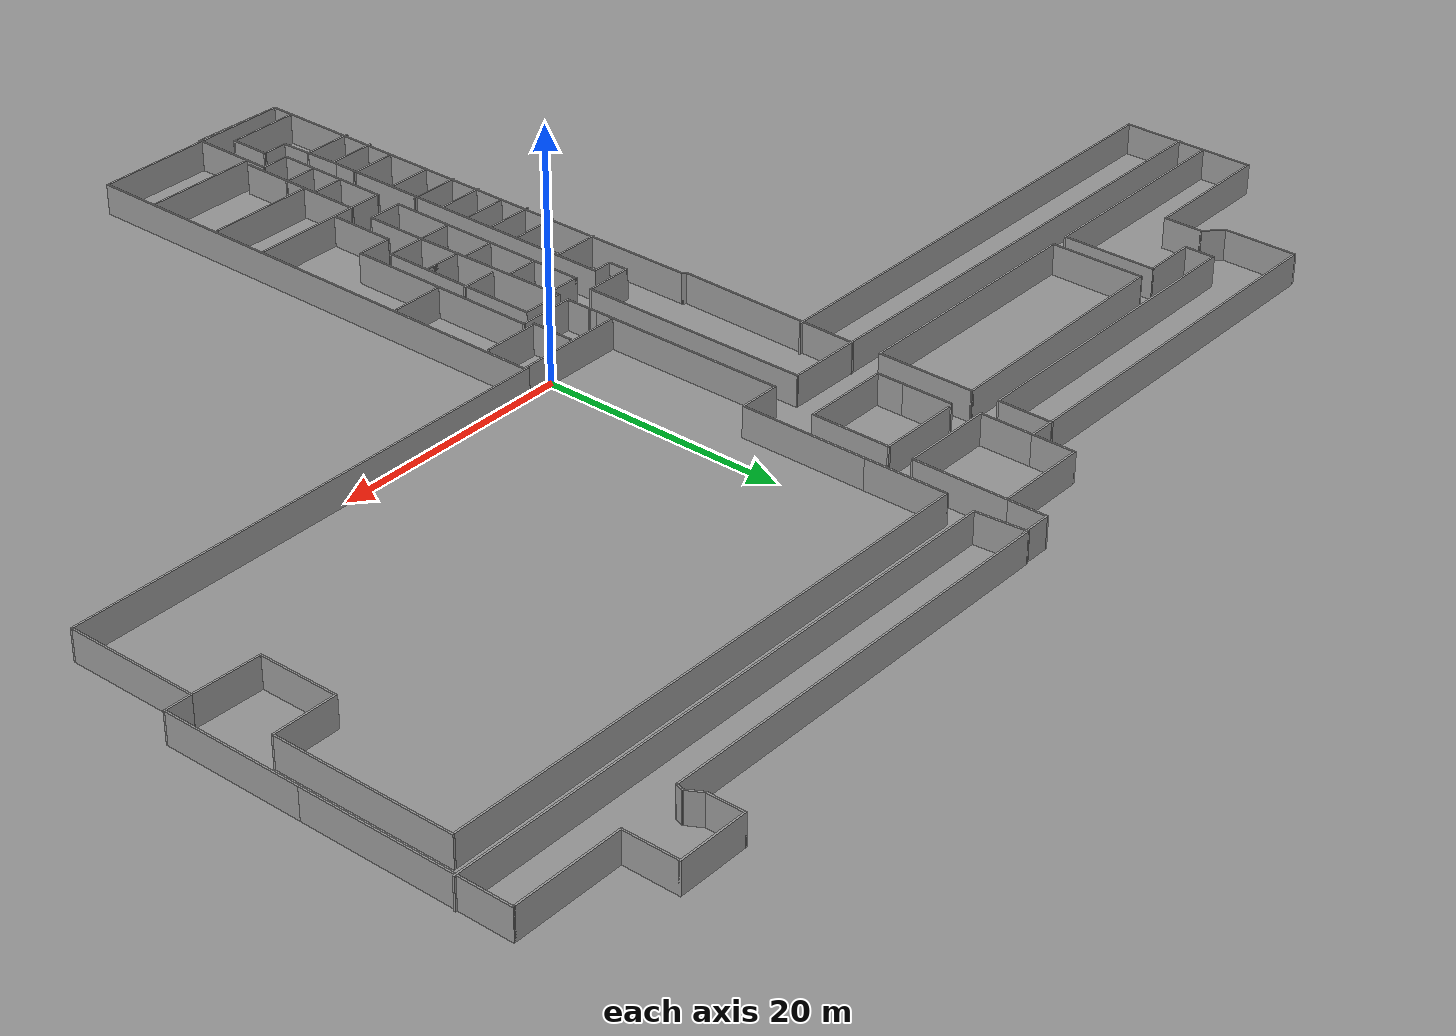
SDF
<sdf version="1.6">
 <world name="default">
  <light name="sun" type="directional">
   <pose>0 0 10 0 -0 0</pose>
   <diffuse>0.8 0.8 0.8 1</diffuse>
   <specular>0.2 0.2 0.2 1</specular>
   <attenuation>
    <range>1000</range>
    <constant>0.9</constant>
    <linear>0.01</linear>
    <quadratic>0.001</quadratic>
   </attenuation>
   <direction>0.5 0.1 -0.9</direction>
  </light>
  <scene><ambient>0.4 0.4 0.4 1</ambient><background>0.7 0.7 0.7 1</background><shadows>1</shadows></scene>
  <physics name="default_physics" default="0" type="ode">
   <max_step_size>0.01</max_step_size>
   <real_time_factor>1</real_time_factor>
   <real_time_update_rate>100</real_time_update_rate>
  </physics>
  <model name="ground_plane_0">
   <static>1</static>
   <link name="link">
    <collision name="collision">
     <geometry><plane><normal>0 0 1</normal><size>100 100</size></plane></geometry>
     <surface><friction><ode><mu>100</mu><mu2>50</mu2></ode></friction></surface>
    </collision>
    <visual name="visual">
     <cast_shadows>0</cast_shadows>
     <geometry><plane><normal>0 0 1</normal><size>100 100</size></plane></geometry>
     <material>
      <script><uri>file://media/materials/scripts/gazebo.material</uri><name>Gazebo/Grey</name></script>
     </material>
    </visual>
    <velocity_decay><linear>0</linear><angular>0</angular></velocity_decay>
   </link>
   <pose>0.497681 0 0 0 -0 0</pose>
  </model>
  <model name="Wean4Complete">
   <pose>-5 0 0 0 -0 0</pose>
   <link name="Wall_0">
    <collision name="Wall_0_Collision">
     <geometry><box><size>34.5 0.15 2.5</size></box></geometry>
     <pose>0 0 1.25 0 -0 0</pose>
    </collision>
    <visual name="Wall_0_Visual">
     <pose>0 0 1.25 0 -0 0</pose>
     <geometry><box><size>34.5 0.15 2.5</size></box></geometry>
     <material>
      <script><uri>file://media/materials/scripts/gazebo.material</uri><name>Gazebo/Grey</name></script>
      <ambient>1 1 1 1</ambient>
     </material>
    </visual>
    <pose>19.3501 38.1931 0 0 -0 0</pose>
   </link>
   <link name="Wall_1">
    <collision name="Wall_1_Collision">
     <geometry><box><size>0.75 0.15 2.5</size></box></geometry>
     <pose>0 0 1.25 0 -0 0</pose>
    </collision>
    <visual name="Wall_1_Visual">
     <pose>0 0 1.25 0 -0 0</pose>
     <geometry><box><size>0.75 0.15 2.5</size></box></geometry>
     <material>
      <script><uri>file://media/materials/scripts/gazebo.material</uri><name>Gazebo/Grey</name></script>
      <ambient>1 1 1 1</ambient>
     </material>
    </visual>
    <pose>36.6027 38.4829 0 0 -0 1.309</pose>
   </link>
   <link name="Wall_10">
    <collision name="Wall_10_Collision">
     <geometry><box><size>2.25 0.15 2.5</size></box></geometry>
     <pose>0 0 1.25 0 -0 0</pose>
    </collision>
    <visual name="Wall_10_Visual">
     <pose>0 0 1.25 0 -0 0</pose>
     <geometry><box><size>2.25 0.15 2.5</size></box></geometry>
     <material>
      <script><uri>file://media/materials/scripts/gazebo.material</uri><name>Gazebo/Grey</name></script>
      <ambient>1 1 1 1</ambient>
     </material>
    </visual>
    <pose>49.4054 10.7418 0 0 -0 3.14159</pose>
   </link>
   <link name="Wall_100">
    <collision name="Wall_100_Collision">
     <geometry><box><size>11.75 0.15 2.5</size></box></geometry>
     <pose>0 0 1.25 0 -0 0</pose>
    </collision>
    <visual name="Wall_100_Visual">
     <pose>0 0 1.25 0 -0 0</pose>
     <geometry><box><size>11.75 0.15 2.5</size></box></geometry>
     <material>
      <script><uri>file://media/materials/scripts/gazebo.material</uri><name>Gazebo/Grey</name></script>
      <ambient>1 1 1 1</ambient>
     </material>
    </visual>
    <pose>1.71451 -25.9001 0 0 -0 3.14159</pose>
   </link>
   <link name="Wall_102">
    <collision name="Wall_102_Collision">
     <geometry><box><size>5.75 0.15 2.5</size></box></geometry>
     <pose>0 0 1.25 0 -0 0</pose>
    </collision>
    <visual name="Wall_102_Visual">
     <pose>0 0 1.25 0 -0 0</pose>
     <geometry><box><size>5.75 0.15 2.5</size></box></geometry>
     <material>
      <script><uri>file://media/materials/scripts/gazebo.material</uri><name>Gazebo/Grey</name></script>
      <ambient>1 1 1 1</ambient>
     </material>
    </visual>
    <pose>0.328372 -23.1001 0 0 -0 1.5708</pose>
   </link>
   <link name="Wall_103">
    <collision name="Wall_103_Collision">
     <geometry><box><size>3 0.15 2.5</size></box></geometry>
     <pose>0 0 1.25 0 -0 0</pose>
    </collision>
    <visual name="Wall_103_Visual">
     <pose>0 0 1.25 0 -0 0</pose>
     <geometry><box><size>3 0.15 2.5</size></box></geometry>
     <material>
      <script><uri>file://media/materials/scripts/gazebo.material</uri><name>Gazebo/Grey</name></script>
      <ambient>1 1 1 1</ambient>
     </material>
    </visual>
    <pose>1.75337 -20.3001 0 0 -0 0</pose>
   </link>
   <link name="Wall_104">
    <collision name="Wall_104_Collision">
     <geometry><box><size>16.25 0.15 2.5</size></box></geometry>
     <pose>0 0 1.25 0 -0 0</pose>
    </collision>
    <visual name="Wall_104_Visual">
     <pose>0 0 1.25 0 -0 0</pose>
     <geometry><box><size>16.25 0.15 2.5</size></box></geometry>
     <material>
      <script><uri>file://media/materials/scripts/gazebo.material</uri><name>Gazebo/Grey</name></script>
      <ambient>1 1 1 1</ambient>
     </material>
    </visual>
    <pose>3.17837 -12.2501 0 0 -0 1.5708</pose>
   </link>
   <link name="Wall_105">
    <collision name="Wall_105_Collision">
     <geometry><box><size>4.75 0.15 2.5</size></box></geometry>
     <pose>0 0 1.25 0 -0 0</pose>
    </collision>
    <visual name="Wall_105_Visual">
     <pose>0 0 1.25 0 -0 0</pose>
     <geometry><box><size>4.75 0.15 2.5</size></box></geometry>
     <material>
      <script><uri>file://media/materials/scripts/gazebo.material</uri><name>Gazebo/Grey</name></script>
      <ambient>1 1 1 1</ambient>
     </material>
    </visual>
    <pose>0.878372 -4.20012 0 0 -0 3.14159</pose>
   </link>
   <link name="Wall_107">
    <collision name="Wall_107_Collision">
     <geometry><box><size>4.5 0.15 2.5</size></box></geometry>
     <pose>0 0 1.25 0 -0 0</pose>
    </collision>
    <visual name="Wall_107_Visual">
     <pose>0 0 1.25 0 -0 0</pose>
     <geometry><box><size>4.5 0.15 2.5</size></box></geometry>
     <material>
      <script><uri>file://media/materials/scripts/gazebo.material</uri><name>Gazebo/Grey</name></script>
      <ambient>1 1 1 1</ambient>
     </material>
    </visual>
    <pose>5.17251 -3.6231 0 0 -0 0</pose>
   </link>
   <link name="Wall_109">
    <collision name="Wall_109_Collision">
     <geometry><box><size>3.5 0.15 2.5</size></box></geometry>
     <pose>0 0 1.25 0 -0 0</pose>
    </collision>
    <visual name="Wall_109_Visual">
     <pose>0 0 1.25 0 -0 0</pose>
     <geometry><box><size>3.5 0.15 2.5</size></box></geometry>
     <material>
      <script><uri>file://media/materials/scripts/gazebo.material</uri><name>Gazebo/Grey</name></script>
      <ambient>1 1 1 1</ambient>
     </material>
    </visual>
    <pose>2.68953 -2.01301 0 0 0 -1.5708</pose>
   </link>
   <link name="Wall_11">
    <collision name="Wall_11_Collision">
     <geometry><box><size>10.75 0.15 2.5</size></box></geometry>
     <pose>0 0 1.25 0 -0 0</pose>
    </collision>
    <visual name="Wall_11_Visual">
     <pose>0 0 1.25 0 -0 0</pose>
     <geometry><box><size>10.75 0.15 2.5</size></box></geometry>
     <material>
      <script><uri>file://media/materials/scripts/gazebo.material</uri><name>Gazebo/Grey</name></script>
      <ambient>1 1 1 1</ambient>
     </material>
    </visual>
    <pose>48.3554 5.44178 0 0 0 -1.5708</pose>
   </link>
   <link name="Wall_111">
    <collision name="Wall_111_Collision">
     <geometry><box><size>4.25 0.15 2.5</size></box></geometry>
     <pose>0 0 1.25 0 -0 0</pose>
    </collision>
    <visual name="Wall_111_Visual">
     <pose>0 0 1.25 0 -0 0</pose>
     <geometry><box><size>4.25 0.15 2.5</size></box></geometry>
     <material>
      <script><uri>file://media/materials/scripts/gazebo.material</uri><name>Gazebo/Grey</name></script>
      <ambient>1 1 1 1</ambient>
     </material>
    </visual>
    <pose>5.36185 -12.4518 0 0 -0 3.14159</pose>
   </link>
   <link name="Wall_113">
    <collision name="Wall_113_Collision">
     <geometry><box><size>3.5 0.15 2.5</size></box></geometry>
     <pose>0 0 1.25 0 -0 0</pose>
    </collision>
    <visual name="Wall_113_Visual">
     <pose>0 0 1.25 0 -0 0</pose>
     <geometry><box><size>3.5 0.15 2.5</size></box></geometry>
     <material>
      <script><uri>file://media/materials/scripts/gazebo.material</uri><name>Gazebo/Grey</name></script>
      <ambient>1 1 1 1</ambient>
     </material>
    </visual>
    <pose>0.155509 -5.16299 0 0 -0 0</pose>
   </link>
   <link name="Wall_114">
    <collision name="Wall_114_Collision">
     <geometry><box><size>13.5 0.15 2.5</size></box></geometry>
     <pose>0 0 1.25 0 -0 0</pose>
    </collision>
    <visual name="Wall_114_Visual">
     <pose>0 0 1.25 0 -0 0</pose>
     <geometry><box><size>13.5 0.15 2.5</size></box></geometry>
     <material>
      <script><uri>file://media/materials/scripts/gazebo.material</uri><name>Gazebo/Grey</name></script>
      <ambient>1 1 1 1</ambient>
     </material>
    </visual>
    <pose>1.83051 -11.838 0 0 0 -1.5708</pose>
   </link>
   <link name="Wall_115">
    <collision name="Wall_115_Collision">
     <geometry><box><size>3.25 0.15 2.5</size></box></geometry>
     <pose>0 0 1.25 0 -0 0</pose>
    </collision>
    <visual name="Wall_115_Visual">
     <pose>0 0 1.25 0 -0 0</pose>
     <geometry><box><size>3.25 0.15 2.5</size></box></geometry>
     <material>
      <script><uri>file://media/materials/scripts/gazebo.material</uri><name>Gazebo/Grey</name></script>
      <ambient>1 1 1 1</ambient>
     </material>
    </visual>
    <pose>0.280509 -18.513 0 0 -0 3.14159</pose>
   </link>
   <link name="Wall_116">
    <collision name="Wall_116_Collision">
     <geometry><box><size>5.25 0.15 2.5</size></box></geometry>
     <pose>0 0 1.25 0 -0 0</pose>
    </collision>
    <visual name="Wall_116_Visual">
     <pose>0 0 1.25 0 -0 0</pose>
     <geometry><box><size>5.25 0.15 2.5</size></box></geometry>
     <material>
      <script><uri>file://media/materials/scripts/gazebo.material</uri><name>Gazebo/Grey</name></script>
      <ambient>1 1 1 1</ambient>
     </material>
    </visual>
    <pose>-1.26949 -21.063 0 0 0 -1.5708</pose>
   </link>
   <link name="Wall_117">
    <collision name="Wall_117_Collision">
     <geometry><box><size>3 0.15 2.5</size></box></geometry>
     <pose>0 0 1.25 0 -0 0</pose>
    </collision>
    <visual name="Wall_117_Visual">
     <pose>0 0 1.25 0 -0 0</pose>
     <geometry><box><size>3 0.15 2.5</size></box></geometry>
     <material>
      <script><uri>file://media/materials/scripts/gazebo.material</uri><name>Gazebo/Grey</name></script>
      <ambient>1 1 1 1</ambient>
     </material>
    </visual>
    <pose>-2.69449 -23.613 0 0 -0 3.14159</pose>
   </link>
   <link name="Wall_119">
    <collision name="Wall_119_Collision">
     <geometry><box><size>3 0.15 2.5</size></box></geometry>
     <pose>0 0 1.25 0 -0 0</pose>
    </collision>
    <visual name="Wall_119_Visual">
     <pose>0 0 1.25 0 -0 0</pose>
     <geometry><box><size>3 0.15 2.5</size></box></geometry>
     <material>
      <script><uri>file://media/materials/scripts/gazebo.material</uri><name>Gazebo/Grey</name></script>
      <ambient>1 1 1 1</ambient>
     </material>
    </visual>
    <pose>0.316145 -14.9156 0 0 -0 0</pose>
   </link>
   <link name="Wall_12">
    <collision name="Wall_12_Collision">
     <geometry><box><size>41 0.15 2.5</size></box></geometry>
     <pose>0 0 1.25 0 -0 0</pose>
    </collision>
    <visual name="Wall_12_Visual">
     <pose>0 0 1.25 0 -0 0</pose>
     <geometry><box><size>41 0.15 2.5</size></box></geometry>
     <material>
      <script><uri>file://media/materials/scripts/gazebo.material</uri><name>Gazebo/Grey</name></script>
      <ambient>1 1 1 1</ambient>
     </material>
    </visual>
    <pose>27.9304 0.141784 0 0 -0 3.14159</pose>
   </link>
   <link name="Wall_120">
    <collision name="Wall_120_Collision">
     <geometry><box><size>3.25 0.15 2.5</size></box></geometry>
     <pose>0 0 1.25 0 -0 0</pose>
    </collision>
    <visual name="Wall_120_Visual">
     <pose>0 0 1.25 0 -0 0</pose>
     <geometry><box><size>3.25 0.15 2.5</size></box></geometry>
     <material>
      <script><uri>file://media/materials/scripts/gazebo.material</uri><name>Gazebo/Grey</name></script>
      <ambient>1 1 1 1</ambient>
     </material>
    </visual>
    <pose>0.191145 -14.9156 0 0 -0 3.14159</pose>
   </link>
   <link name="Wall_122">
    <collision name="Wall_122_Collision">
     <geometry><box><size>3 0.15 2.5</size></box></geometry>
     <pose>0 0 1.25 0 -0 0</pose>
    </collision>
    <visual name="Wall_122_Visual">
     <pose>0 0 1.25 0 -0 0</pose>
     <geometry><box><size>3 0.15 2.5</size></box></geometry>
     <material>
      <script><uri>file://media/materials/scripts/gazebo.material</uri><name>Gazebo/Grey</name></script>
      <ambient>1 1 1 1</ambient>
     </material>
    </visual>
    <pose>0.545917 -11.0146 0 0 -0 3.14159</pose>
   </link>
   <link name="Wall_124">
    <collision name="Wall_124_Collision">
     <geometry><box><size>12.7839 0.15 2.5</size></box></geometry>
     <pose>0 0 1.25 0 -0 0</pose>
    </collision>
    <visual name="Wall_124_Visual">
     <pose>0 0 1.25 0 -0 0</pose>
     <geometry><box><size>12.7839 0.15 2.5</size></box></geometry>
     <material>
      <script><uri>file://media/materials/scripts/gazebo.material</uri><name>Gazebo/Grey</name></script>
      <ambient>1 1 1 1</ambient>
     </material>
    </visual>
    <pose>-1.39449 -12.1973 0 0 0 -1.55101</pose>
   </link>
   <link name="Wall_125">
    <collision name="Wall_125_Collision">
     <geometry><box><size>2.75 0.15 2.5</size></box></geometry>
     <pose>0 0 1.25 0 -0 0</pose>
    </collision>
    <visual name="Wall_125_Visual">
     <pose>0 0 1.25 0 -0 0</pose>
     <geometry><box><size>2.75 0.15 2.5</size></box></geometry>
     <material>
      <script><uri>file://media/materials/scripts/gazebo.material</uri><name>Gazebo/Grey</name></script>
      <ambient>1 1 1 1</ambient>
     </material>
    </visual>
    <pose>-2.56949 -18.513 0 0 -0 3.14159</pose>
   </link>
   <link name="Wall_127">
    <collision name="Wall_127_Collision">
     <geometry><box><size>2.5 0.15 2.5</size></box></geometry>
     <pose>0 0 1.25 0 -0 0</pose>
    </collision>
    <visual name="Wall_127_Visual">
     <pose>0 0 1.25 0 -0 0</pose>
     <geometry><box><size>2.5 0.15 2.5</size></box></geometry>
     <material>
      <script><uri>file://media/materials/scripts/gazebo.material</uri><name>Gazebo/Grey</name></script>
      <ambient>1 1 1 1</ambient>
     </material>
    </visual>
    <pose>-2.79715 -14.197 0 0 -0 3.14159</pose>
   </link>
   <link name="Wall_129">
    <collision name="Wall_129_Collision">
     <geometry><box><size>2.5 0.15 2.5</size></box></geometry>
     <pose>0 0 1.25 0 -0 0</pose>
    </collision>
    <visual name="Wall_129_Visual">
     <pose>0 0 1.25 0 -0 0</pose>
     <geometry><box><size>2.5 0.15 2.5</size></box></geometry>
     <material>
      <script><uri>file://media/materials/scripts/gazebo.material</uri><name>Gazebo/Grey</name></script>
      <ambient>1 1 1 1</ambient>
     </material>
    </visual>
    <pose>-2.79715 -9.8853 0 0 -0 3.14159</pose>
   </link>
   <link name="Wall_13">
    <collision name="Wall_13_Collision">
     <geometry><box><size>0.16 0.15 2.5</size></box></geometry>
     <pose>0 0 1.25 0 -0 0</pose>
    </collision>
    <visual name="Wall_13_Visual">
     <pose>0 0 1.25 0 -0 0</pose>
     <geometry><box><size>0.16 0.15 2.5</size></box></geometry>
     <material>
      <script><uri>file://media/materials/scripts/gazebo.material</uri><name>Gazebo/Grey</name></script>
      <ambient>1 1 1 1</ambient>
     </material>
    </visual>
    <pose>7.51037 0.141784 0 0 -0 0</pose>
   </link>
   <link name="Wall_131">
    <collision name="Wall_131_Collision">
     <geometry><box><size>4 0.15 2.5</size></box></geometry>
     <pose>0 0 1.25 0 -0 0</pose>
    </collision>
    <visual name="Wall_131_Visual">
     <pose>0 0 1.25 0 -0 0</pose>
     <geometry><box><size>4 0.15 2.5</size></box></geometry>
     <material>
      <script><uri>file://media/materials/scripts/gazebo.material</uri><name>Gazebo/Grey</name></script>
      <ambient>1 1 1 1</ambient>
     </material>
    </visual>
    <pose>-7.80722 -9.16669 0 0 -0 0</pose>
   </link>
   <link name="Wall_132">
    <collision name="Wall_132_Collision">
     <geometry><box><size>0.15 0.15 2.5</size></box></geometry>
     <pose>0 0 1.25 0 -0 0</pose>
    </collision>
    <visual name="Wall_132_Visual">
     <pose>0 0 1.25 0 -0 0</pose>
     <geometry><box><size>0.15 0.15 2.5</size></box></geometry>
     <material>
      <script><uri>file://media/materials/scripts/gazebo.material</uri><name>Gazebo/Grey</name></script>
      <ambient>1 1 1 1</ambient>
     </material>
    </visual>
    <pose>-5.88222 -9.16669 0 0 -0 0</pose>
   </link>
   <link name="Wall_134">
    <collision name="Wall_134_Collision">
     <geometry><box><size>3.75 0.15 2.5</size></box></geometry>
     <pose>0 0 1.25 0 -0 0</pose>
    </collision>
    <visual name="Wall_134_Visual">
     <pose>0 0 1.25 0 -0 0</pose>
     <geometry><box><size>3.75 0.15 2.5</size></box></geometry>
     <material>
      <script><uri>file://media/materials/scripts/gazebo.material</uri><name>Gazebo/Grey</name></script>
      <ambient>1 1 1 1</ambient>
     </material>
    </visual>
    <pose>-7.93222 -13.2731 0 0 -0 0</pose>
   </link>
   <link name="Wall_136">
    <collision name="Wall_136_Collision">
     <geometry><box><size>4 0.15 2.5</size></box></geometry>
     <pose>0 0 1.25 0 -0 0</pose>
    </collision>
    <visual name="Wall_136_Visual">
     <pose>0 0 1.25 0 -0 0</pose>
     <geometry><box><size>4 0.15 2.5</size></box></geometry>
     <material>
      <script><uri>file://media/materials/scripts/gazebo.material</uri><name>Gazebo/Grey</name></script>
      <ambient>1 1 1 1</ambient>
     </material>
    </visual>
    <pose>-7.90988 -15.8395 0 0 -0 0</pose>
   </link>
   <link name="Wall_138">
    <collision name="Wall_138_Collision">
     <geometry><box><size>3.75 0.15 2.5</size></box></geometry>
     <pose>0 0 1.25 0 -0 0</pose>
    </collision>
    <visual name="Wall_138_Visual">
     <pose>0 0 1.25 0 -0 0</pose>
     <geometry><box><size>3.75 0.15 2.5</size></box></geometry>
     <material>
      <script><uri>file://media/materials/scripts/gazebo.material</uri><name>Gazebo/Grey</name></script>
      <ambient>1 1 1 1</ambient>
     </material>
    </visual>
    <pose>-7.7269 -18.2007 0 0 -0 0</pose>
   </link>
   <link name="Wall_140">
    <collision name="Wall_140_Collision">
     <geometry><box><size>4.25 0.15 2.5</size></box></geometry>
     <pose>0 0 1.25 0 -0 0</pose>
    </collision>
    <visual name="Wall_140_Visual">
     <pose>0 0 1.25 0 -0 0</pose>
     <geometry><box><size>4.25 0.15 2.5</size></box></geometry>
     <material>
      <script><uri>file://media/materials/scripts/gazebo.material</uri><name>Gazebo/Grey</name></script>
      <ambient>1 1 1 1</ambient>
     </material>
    </visual>
    <pose>-7.68222 -23.3336 0 0 -0 0</pose>
   </link>
   <link name="Wall_142">
    <collision name="Wall_142_Collision">
     <geometry><box><size>4 0.15 2.5</size></box></geometry>
     <pose>0 0 1.25 0 -0 0</pose>
    </collision>
    <visual name="Wall_142_Visual">
     <pose>0 0 1.25 0 -0 0</pose>
     <geometry><box><size>4 0.15 2.5</size></box></geometry>
     <material>
      <script><uri>file://media/materials/scripts/gazebo.material</uri><name>Gazebo/Grey</name></script>
      <ambient>1 1 1 1</ambient>
     </material>
    </visual>
    <pose>-7.80722 -20.7672 0 0 -0 0</pose>
   </link>
   <link name="Wall_144">
    <collision name="Wall_144_Collision">
     <geometry><box><size>4 0.15 2.5</size></box></geometry>
     <pose>0 0 1.25 0 -0 0</pose>
    </collision>
    <visual name="Wall_144_Visual">
     <pose>0 0 1.25 0 -0 0</pose>
     <geometry><box><size>4 0.15 2.5</size></box></geometry>
     <material>
      <script><uri>file://media/materials/scripts/gazebo.material</uri><name>Gazebo/Grey</name></script>
      <ambient>1 1 1 1</ambient>
     </material>
    </visual>
    <pose>-7.6019 -29.8012 0 0 -0 0</pose>
   </link>
   <link name="Wall_146">
    <collision name="Wall_146_Collision">
     <geometry><box><size>3.5 0.15 2.5</size></box></geometry>
     <pose>0 0 1.25 0 -0 0</pose>
    </collision>
    <visual name="Wall_146_Visual">
     <pose>0 0 1.25 0 -0 0</pose>
     <geometry><box><size>3.5 0.15 2.5</size></box></geometry>
     <material>
      <script><uri>file://media/materials/scripts/gazebo.material</uri><name>Gazebo/Grey</name></script>
      <ambient>1 1 1 1</ambient>
     </material>
    </visual>
    <pose>-7.74924 -26.0028 0 0 -0 0</pose>
   </link>
   <link name="Wall_148">
    <collision name="Wall_148_Collision">
     <geometry><box><size>4 0.15 2.5</size></box></geometry>
     <pose>0 0 1.25 0 -0 0</pose>
    </collision>
    <visual name="Wall_148_Visual">
     <pose>0 0 1.25 0 -0 0</pose>
     <geometry><box><size>4 0.15 2.5</size></box></geometry>
     <material>
      <script><uri>file://media/materials/scripts/gazebo.material</uri><name>Gazebo/Grey</name></script>
      <ambient>1 1 1 1</ambient>
     </material>
    </visual>
    <pose>-7.90988 -32.265 0 0 -0 0</pose>
   </link>
   <link name="Wall_15">
    <collision name="Wall_15_Collision">
     <geometry><box><size>17.5 0.15 2.5</size></box></geometry>
     <pose>0 0 1.25 0 -0 0</pose>
    </collision>
    <visual name="Wall_15_Visual">
     <pose>0 0 1.25 0 -0 0</pose>
     <geometry><box><size>17.5 0.15 2.5</size></box></geometry>
     <material>
      <script><uri>file://media/materials/scripts/gazebo.material</uri><name>Gazebo/Grey</name></script>
      <ambient>1 1 1 1</ambient>
     </material>
    </visual>
    <pose>-0.933063 -42.5844 0 0 -0 3.14159</pose>
   </link>
   <link name="Wall_150">
    <collision name="Wall_150_Collision">
     <geometry><box><size>4.25 0.15 2.5</size></box></geometry>
     <pose>0 0 1.25 0 -0 0</pose>
    </collision>
    <visual name="Wall_150_Visual">
     <pose>0 0 1.25 0 -0 0</pose>
     <geometry><box><size>4.25 0.15 2.5</size></box></geometry>
     <material>
      <script><uri>file://media/materials/scripts/gazebo.material</uri><name>Gazebo/Grey</name></script>
      <ambient>1 1 1 1</ambient>
     </material>
    </visual>
    <pose>-7.78488 -34.8315 0 0 -0 0</pose>
   </link>
   <link name="Wall_152">
    <collision name="Wall_152_Collision">
     <geometry><box><size>2.75 0.15 2.5</size></box></geometry>
     <pose>0 0 1.25 0 -0 0</pose>
    </collision>
    <visual name="Wall_152_Visual">
     <pose>0 0 1.25 0 -0 0</pose>
     <geometry><box><size>2.75 0.15 2.5</size></box></geometry>
     <material>
      <script><uri>file://media/materials/scripts/gazebo.material</uri><name>Gazebo/Grey</name></script>
      <ambient>1 1 1 1</ambient>
     </material>
    </visual>
    <pose>-2.68331 -32.6756 0 0 -0 0</pose>
   </link>
   <link name="Wall_154">
    <collision name="Wall_154_Collision">
     <geometry><box><size>11.25 0.15 2.5</size></box></geometry>
     <pose>0 0 1.25 0 -0 0</pose>
    </collision>
    <visual name="Wall_154_Visual">
     <pose>0 0 1.25 0 -0 0</pose>
     <geometry><box><size>11.25 0.15 2.5</size></box></geometry>
     <material>
      <script><uri>file://media/materials/scripts/gazebo.material</uri><name>Gazebo/Grey</name></script>
      <ambient>1 1 1 1</ambient>
     </material>
    </visual>
    <pose>-1.41683 -31.3475 0 0 0 -1.5708</pose>
   </link>
   <link name="Wall_157">
    <collision name="Wall_157_Collision">
     <geometry><box><size>2.75 0.15 2.5</size></box></geometry>
     <pose>0 0 1.25 0 -0 0</pose>
    </collision>
    <visual name="Wall_157_Visual">
     <pose>0 0 1.25 0 -0 0</pose>
     <geometry><box><size>2.75 0.15 2.5</size></box></geometry>
     <material>
      <script><uri>file://media/materials/scripts/gazebo.material</uri><name>Gazebo/Grey</name></script>
      <ambient>1 1 1 1</ambient>
     </material>
    </visual>
    <pose>-2.88863 -29.8012 0 0 -0 0</pose>
   </link>
   <link name="Wall_159">
    <collision name="Wall_159_Collision">
     <geometry><box><size>2.25 0.15 2.5</size></box></geometry>
     <pose>0 0 1.25 0 -0 0</pose>
    </collision>
    <visual name="Wall_159_Visual">
     <pose>0 0 1.25 0 -0 0</pose>
     <geometry><box><size>2.25 0.15 2.5</size></box></geometry>
     <material>
      <script><uri>file://media/materials/scripts/gazebo.material</uri><name>Gazebo/Grey</name></script>
      <ambient>1 1 1 1</ambient>
     </material>
    </visual>
    <pose>-1.42163 -3.15012 0 0 -0 1.5708</pose>
   </link>
   <link name="Wall_16">
    <collision name="Wall_16_Collision">
     <geometry><box><size>42.25 0.15 2.5</size></box></geometry>
     <pose>0 0 1.25 0 -0 0</pose>
    </collision>
    <visual name="Wall_16_Visual">
     <pose>0 0 1.25 0 -0 0</pose>
     <geometry><box><size>42.25 0.15 2.5</size></box></geometry>
     <material>
      <script><uri>file://media/materials/scripts/gazebo.material</uri><name>Gazebo/Grey</name></script>
      <ambient>1 1 1 1</ambient>
     </material>
    </visual>
    <pose>-9.60806 -21.5344 0 0 -0 1.5708</pose>
   </link>
   <link name="Wall_160">
    <collision name="Wall_160_Collision">
     <geometry><box><size>0.819298 0.15 2.5</size></box></geometry>
     <pose>0 0 1.25 0 -0 0</pose>
    </collision>
    <visual name="Wall_160_Visual">
     <pose>0 0 1.25 0 -0 0</pose>
     <geometry><box><size>0.819298 0.15 2.5</size></box></geometry>
     <material>
      <script><uri>file://media/materials/scripts/gazebo.material</uri><name>Gazebo/Grey</name></script>
      <ambient>1 1 1 1</ambient>
     </material>
    </visual>
    <pose>-1.43719 -1.76583 0 0 -0 1.6173</pose>
   </link>
   <link name="Wall_163">
    <collision name="Wall_163_Collision">
     <geometry><box><size>17.8814 0.15 2.5</size></box></geometry>
     <pose>0 0 1.25 0 -0 0</pose>
    </collision>
    <visual name="Wall_163_Visual">
     <pose>0 0 1.25 0 -0 0</pose>
     <geometry><box><size>17.8814 0.15 2.5</size></box></geometry>
     <material>
      <script><uri>file://media/materials/scripts/gazebo.material</uri><name>Gazebo/Grey</name></script>
      <ambient>1 1 1 1</ambient>
     </material>
    </visual>
    <pose>-4.11949 -14.7473 0 0 -0 1.5708</pose>
   </link>
   <link name="Wall_17">
    <collision name="Wall_17_Collision">
     <geometry><box><size>0.5 0.15 2.5</size></box></geometry>
     <pose>0 0 1.25 0 -0 0</pose>
    </collision>
    <visual name="Wall_17_Visual">
     <pose>0 0 1.25 0 -0 0</pose>
     <geometry><box><size>0.5 0.15 2.5</size></box></geometry>
     <material>
      <script><uri>file://media/materials/scripts/gazebo.material</uri><name>Gazebo/Grey</name></script>
      <ambient>1 1 1 1</ambient>
     </material>
    </visual>
    <pose>-9.73181 -0.360694 0 0 -0 2.35619</pose>
   </link>
   <link name="Wall_19">
    <collision name="Wall_19_Collision">
     <geometry><box><size>42.75 0.15 2.5</size></box></geometry>
     <pose>0 0 1.25 0 -0 0</pose>
    </collision>
    <visual name="Wall_19_Visual">
     <pose>0 0 1.25 0 -0 0</pose>
     <geometry><box><size>42.75 0.15 2.5</size></box></geometry>
     <material>
      <script><uri>file://media/materials/scripts/gazebo.material</uri><name>Gazebo/Grey</name></script>
      <ambient>1 1 1 1</ambient>
     </material>
    </visual>
    <pose>7.74194 -21.2844 0 0 -0 1.5708</pose>
   </link>
   <link name="Wall_2">
    <collision name="Wall_2_Collision">
     <geometry><box><size>1.5 0.15 2.5</size></box></geometry>
     <pose>0 0 1.25 0 -0 0</pose>
    </collision>
    <visual name="Wall_2_Visual">
     <pose>0 0 1.25 0 -0 0</pose>
     <geometry><box><size>1.5 0.15 2.5</size></box></geometry>
     <material>
      <script><uri>file://media/materials/scripts/gazebo.material</uri><name>Gazebo/Grey</name></script>
      <ambient>1 1 1 1</ambient>
     </material>
    </visual>
    <pose>36.3429 39.3572 0 0 -0 2.0944</pose>
   </link>
   <link name="Wall_21">
    <collision name="Wall_21_Collision">
     <geometry><box><size>9.25 0.15 2.5</size></box></geometry>
     <pose>0 0 1.25 0 -0 0</pose>
    </collision>
    <visual name="Wall_21_Visual">
     <pose>0 0 1.25 0 -0 0</pose>
     <geometry><box><size>9.25 0.15 2.5</size></box></geometry>
     <material>
      <script><uri>file://media/materials/scripts/gazebo.material</uri><name>Gazebo/Grey</name></script>
      <ambient>1 1 1 1</ambient>
     </material>
    </visual>
    <pose>3.19194 0.015563 0 0 -0 3.14159</pose>
   </link>
   <link name="Wall_23">
    <collision name="Wall_23_Collision">
     <geometry><box><size>16.25 0.15 2.5</size></box></geometry>
     <pose>0 0 1.25 0 -0 0</pose>
    </collision>
    <visual name="Wall_23_Visual">
     <pose>0 0 1.25 0 -0 0</pose>
     <geometry><box><size>16.25 0.15 2.5</size></box></geometry>
     <material>
      <script><uri>file://media/materials/scripts/gazebo.material</uri><name>Gazebo/Grey</name></script>
      <ambient>1 1 1 1</ambient>
     </material>
    </visual>
    <pose>-1.45274 6.61846 0 0 -0 1.5708</pose>
   </link>
   <link name="Wall_24">
    <collision name="Wall_24_Collision">
     <geometry><box><size>3.5 0.15 2.5</size></box></geometry>
     <pose>0 0 1.25 0 -0 0</pose>
    </collision>
    <visual name="Wall_24_Visual">
     <pose>0 0 1.25 0 -0 0</pose>
     <geometry><box><size>3.5 0.15 2.5</size></box></geometry>
     <material>
      <script><uri>file://media/materials/scripts/gazebo.material</uri><name>Gazebo/Grey</name></script>
      <ambient>1 1 1 1</ambient>
     </material>
    </visual>
    <pose>0.222256 14.6685 0 0 -0 0</pose>
   </link>
   <link name="Wall_25">
    <collision name="Wall_25_Collision">
     <geometry><box><size>10.5 0.15 2.5</size></box></geometry>
     <pose>0 0 1.25 0 -0 0</pose>
    </collision>
    <visual name="Wall_25_Visual">
     <pose>0 0 1.25 0 -0 0</pose>
     <geometry><box><size>10.5 0.15 2.5</size></box></geometry>
     <material>
      <script><uri>file://media/materials/scripts/gazebo.material</uri><name>Gazebo/Grey</name></script>
      <ambient>1 1 1 1</ambient>
     </material>
    </visual>
    <pose>1.89726 19.8435 0 0 -0 1.5708</pose>
   </link>
   <link name="Wall_27">
    <collision name="Wall_27_Collision">
     <geometry><box><size>6.75 0.15 2.5</size></box></geometry>
     <pose>0 0 1.25 0 -0 0</pose>
    </collision>
    <visual name="Wall_27_Visual">
     <pose>0 0 1.25 0 -0 0</pose>
     <geometry><box><size>6.75 0.15 2.5</size></box></geometry>
     <material>
      <script><uri>file://media/materials/scripts/gazebo.material</uri><name>Gazebo/Grey</name></script>
      <ambient>1 1 1 1</ambient>
     </material>
    </visual>
    <pose>1.89726 28.3185 0 0 -0 1.5708</pose>
   </link>
   <link name="Wall_28">
    <collision name="Wall_28_Collision">
     <geometry><box><size>46.25 0.15 2.5</size></box></geometry>
     <pose>0 0 1.25 0 -0 0</pose>
    </collision>
    <visual name="Wall_28_Visual">
     <pose>0 0 1.25 0 -0 0</pose>
     <geometry><box><size>46.25 0.15 2.5</size></box></geometry>
     <material>
      <script><uri>file://media/materials/scripts/gazebo.material</uri><name>Gazebo/Grey</name></script>
      <ambient>1 1 1 1</ambient>
     </material>
    </visual>
    <pose>24.9473 31.6185 0 0 -0 0</pose>
   </link>
   <link name="Wall_29">
    <collision name="Wall_29_Collision">
     <geometry><box><size>14.5 0.15 2.5</size></box></geometry>
     <pose>0 0 1.25 0 -0 0</pose>
    </collision>
    <visual name="Wall_29_Visual">
     <pose>0 0 1.25 0 -0 0</pose>
     <geometry><box><size>14.5 0.15 2.5</size></box></geometry>
     <material>
      <script><uri>file://media/materials/scripts/gazebo.material</uri><name>Gazebo/Grey</name></script>
      <ambient>1 1 1 1</ambient>
     </material>
    </visual>
    <pose>47.9973 24.4435 0 0 0 -1.5708</pose>
   </link>
   <link name="Wall_3">
    <collision name="Wall_3_Collision">
     <geometry><box><size>3 0.15 2.5</size></box></geometry>
     <pose>0 0 1.25 0 -0 0</pose>
    </collision>
    <visual name="Wall_3_Visual">
     <pose>0 0 1.25 0 -0 0</pose>
     <geometry><box><size>3 0.15 2.5</size></box></geometry>
     <material>
      <script><uri>file://media/materials/scripts/gazebo.material</uri><name>Gazebo/Grey</name></script>
      <ambient>1 1 1 1</ambient>
     </material>
    </visual>
    <pose>36.0054 41.3668 0 0 -0 1.5708</pose>
   </link>
   <link name="Wall_30">
    <collision name="Wall_30_Collision">
     <geometry><box><size>5.25 0.15 2.5</size></box></geometry>
     <pose>0 0 1.25 0 -0 0</pose>
    </collision>
    <visual name="Wall_30_Visual">
     <pose>0 0 1.25 0 -0 0</pose>
     <geometry><box><size>5.25 0.15 2.5</size></box></geometry>
     <material>
      <script><uri>file://media/materials/scripts/gazebo.material</uri><name>Gazebo/Grey</name></script>
      <ambient>1 1 1 1</ambient>
     </material>
    </visual>
    <pose>45.4473 17.2685 0 0 -0 3.14159</pose>
   </link>
   <link name="Wall_31">
    <collision name="Wall_31_Collision">
     <geometry><box><size>6.5 0.15 2.5</size></box></geometry>
     <pose>0 0 1.25 0 -0 0</pose>
    </collision>
    <visual name="Wall_31_Visual">
     <pose>0 0 1.25 0 -0 0</pose>
     <geometry><box><size>6.5 0.15 2.5</size></box></geometry>
     <material>
      <script><uri>file://media/materials/scripts/gazebo.material</uri><name>Gazebo/Grey</name></script>
      <ambient>1 1 1 1</ambient>
     </material>
    </visual>
    <pose>42.8973 14.0935 0 0 0 -1.5708</pose>
   </link>
   <link name="Wall_32">
    <collision name="Wall_32_Collision">
     <geometry><box><size>5.61097 0.15 2.5</size></box></geometry>
     <pose>0 0 1.25 0 -0 0</pose>
    </collision>
    <visual name="Wall_32_Visual">
     <pose>0 0 1.25 0 -0 0</pose>
     <geometry><box><size>5.61097 0.15 2.5</size></box></geometry>
     <material>
      <script><uri>file://media/materials/scripts/gazebo.material</uri><name>Gazebo/Grey</name></script>
      <ambient>1 1 1 1</ambient>
     </material>
    </visual>
    <pose>45.6263 10.8301 0 0 0 -0.032358</pose>
   </link>
   <link name="Wall_34">
    <collision name="Wall_34_Collision">
     <geometry><box><size>48.25 0.15 2.5</size></box></geometry>
     <pose>0 0 1.25 0 -0 0</pose>
    </collision>
    <visual name="Wall_34_Visual">
     <pose>0 0 1.25 0 -0 0</pose>
     <geometry><box><size>48.25 0.15 2.5</size></box></geometry>
     <material>
      <script><uri>file://media/materials/scripts/gazebo.material</uri><name>Gazebo/Grey</name></script>
      <ambient>1 1 1 1</ambient>
     </material>
    </visual>
    <pose>26.5409 34.1867 0 0 -0 3.14159</pose>
   </link>
   <link name="Wall_35">
    <collision name="Wall_35_Collision">
     <geometry><box><size>4.16884 0.15 2.5</size></box></geometry>
     <pose>0 0 1.25 0 -0 0</pose>
    </collision>
    <visual name="Wall_35_Visual">
     <pose>0 0 1.25 0 -0 0</pose>
     <geometry><box><size>4.16884 0.15 2.5</size></box></geometry>
     <material>
      <script><uri>file://media/materials/scripts/gazebo.material</uri><name>Gazebo/Grey</name></script>
      <ambient>1 1 1 1</ambient>
     </material>
    </visual>
    <pose>2.33301 36.1899 0 0 -0 1.64947</pose>
   </link>
   <link name="Wall_37">
    <collision name="Wall_37_Collision">
     <geometry><box><size>19 0.15 2.5</size></box></geometry>
     <pose>0 0 1.25 0 -0 0</pose>
    </collision>
    <visual name="Wall_37_Visual">
     <pose>0 0 1.25 0 -0 0</pose>
     <geometry><box><size>19 0.15 2.5</size></box></geometry>
     <material>
      <script><uri>file://media/materials/scripts/gazebo.material</uri><name>Gazebo/Grey</name></script>
      <ambient>1 1 1 1</ambient>
     </material>
    </visual>
    <pose>-3.59519 5.47964 0 0 0 -1.5708</pose>
   </link>
   <link name="Wall_38">
    <collision name="Wall_38_Collision">
     <geometry><box><size>4 0.15 2.5</size></box></geometry>
     <pose>0 0 1.25 0 -0 0</pose>
    </collision>
    <visual name="Wall_38_Visual">
     <pose>0 0 1.25 0 -0 0</pose>
     <geometry><box><size>4 0.15 2.5</size></box></geometry>
     <material>
      <script><uri>file://media/materials/scripts/gazebo.material</uri><name>Gazebo/Grey</name></script>
      <ambient>1 1 1 1</ambient>
     </material>
    </visual>
    <pose>-5.52019 -3.94536 0 0 -0 3.14159</pose>
   </link>
   <link name="Wall_39">
    <collision name="Wall_39_Collision">
     <geometry><box><size>1.75 0.15 2.5</size></box></geometry>
     <pose>0 0 1.25 0 -0 0</pose>
    </collision>
    <visual name="Wall_39_Visual">
     <pose>0 0 1.25 0 -0 0</pose>
     <geometry><box><size>1.75 0.15 2.5</size></box></geometry>
     <material>
      <script><uri>file://media/materials/scripts/gazebo.material</uri><name>Gazebo/Grey</name></script>
      <ambient>1 1 1 1</ambient>
     </material>
    </visual>
    <pose>-7.44519 -4.74536 0 0 0 -1.5708</pose>
   </link>
   <link name="Wall_4">
    <collision name="Wall_4_Collision">
     <geometry><box><size>5.75 0.15 2.5</size></box></geometry>
     <pose>0 0 1.25 0 -0 0</pose>
    </collision>
    <visual name="Wall_4_Visual">
     <pose>0 0 1.25 0 -0 0</pose>
     <geometry><box><size>5.75 0.15 2.5</size></box></geometry>
     <material>
      <script><uri>file://media/materials/scripts/gazebo.material</uri><name>Gazebo/Grey</name></script>
      <ambient>1 1 1 1</ambient>
     </material>
    </visual>
    <pose>38.8054 42.7918 0 0 -0 0</pose>
   </link>
   <link name="Wall_40">
    <collision name="Wall_40_Collision">
     <geometry><box><size>1.75 0.15 2.5</size></box></geometry>
     <pose>0 0 1.25 0 -0 0</pose>
    </collision>
    <visual name="Wall_40_Visual">
     <pose>0 0 1.25 0 -0 0</pose>
     <geometry><box><size>1.75 0.15 2.5</size></box></geometry>
     <material>
      <script><uri>file://media/materials/scripts/gazebo.material</uri><name>Gazebo/Grey</name></script>
      <ambient>1 1 1 1</ambient>
     </material>
    </visual>
    <pose>-6.64519 -5.54536 0 0 -0 0</pose>
   </link>
   <link name="Wall_41">
    <collision name="Wall_41_Collision">
     <geometry><box><size>26.5 0.15 2.5</size></box></geometry>
     <pose>0 0 1.25 0 -0 0</pose>
    </collision>
    <visual name="Wall_41_Visual">
     <pose>0 0 1.25 0 -0 0</pose>
     <geometry><box><size>26.5 0.15 2.5</size></box></geometry>
     <material>
      <script><uri>file://media/materials/scripts/gazebo.material</uri><name>Gazebo/Grey</name></script>
      <ambient>1 1 1 1</ambient>
     </material>
    </visual>
    <pose>-5.84519 -18.7204 0 0 0 -1.5708</pose>
   </link>
   <link name="Wall_43">
    <collision name="Wall_43_Collision">
     <geometry><box><size>6 0.15 2.5</size></box></geometry>
     <pose>0 0 1.25 0 -0 0</pose>
    </collision>
    <visual name="Wall_43_Visual">
     <pose>0 0 1.25 0 -0 0</pose>
     <geometry><box><size>6 0.15 2.5</size></box></geometry>
     <material>
      <script><uri>file://media/materials/scripts/gazebo.material</uri><name>Gazebo/Grey</name></script>
      <ambient>1 1 1 1</ambient>
     </material>
    </visual>
    <pose>-6.47266 -40.7098 0 0 -0 0</pose>
   </link>
   <link name="Wall_44">
    <collision name="Wall_44_Collision">
     <geometry><box><size>3.5 0.15 2.5</size></box></geometry>
     <pose>0 0 1.25 0 -0 0</pose>
    </collision>
    <visual name="Wall_44_Visual">
     <pose>0 0 1.25 0 -0 0</pose>
     <geometry><box><size>3.5 0.15 2.5</size></box></geometry>
     <material>
      <script><uri>file://media/materials/scripts/gazebo.material</uri><name>Gazebo/Grey</name></script>
      <ambient>1 1 1 1</ambient>
     </material>
    </visual>
    <pose>-3.54766 -39.0348 0 0 -0 1.5708</pose>
   </link>
   <link name="Wall_45">
    <collision name="Wall_45_Collision">
     <geometry><box><size>2.25 0.15 2.5</size></box></geometry>
     <pose>0 0 1.25 0 -0 0</pose>
    </collision>
    <visual name="Wall_45_Visual">
     <pose>0 0 1.25 0 -0 0</pose>
     <geometry><box><size>2.25 0.15 2.5</size></box></geometry>
     <material>
      <script><uri>file://media/materials/scripts/gazebo.material</uri><name>Gazebo/Grey</name></script>
      <ambient>1 1 1 1</ambient>
     </material>
    </visual>
    <pose>-4.59766 -37.3598 0 0 -0 3.14159</pose>
   </link>
   <link name="Wall_46">
    <collision name="Wall_46_Collision">
     <geometry><box><size>5.618 0.15 2.5</size></box></geometry>
     <pose>0 0 1.25 0 -0 0</pose>
    </collision>
    <visual name="Wall_46_Visual">
     <pose>0 0 1.25 0 -0 0</pose>
     <geometry><box><size>5.618 0.15 2.5</size></box></geometry>
     <material>
      <script><uri>file://media/materials/scripts/gazebo.material</uri><name>Gazebo/Grey</name></script>
      <ambient>1 1 1 1</ambient>
     </material>
    </visual>
    <pose>-5.74643 -34.6276 0 0 -0 1.60693</pose>
   </link>
   <link name="Wall_48">
    <collision name="Wall_48_Collision">
     <geometry><box><size>15.3834 0.15 2.5</size></box></geometry>
     <pose>0 0 1.25 0 -0 0</pose>
    </collision>
    <visual name="Wall_48_Visual">
     <pose>0 0 1.25 0 -0 0</pose>
     <geometry><box><size>15.3834 0.15 2.5</size></box></geometry>
     <material>
      <script><uri>file://media/materials/scripts/gazebo.material</uri><name>Gazebo/Grey</name></script>
      <ambient>1 1 1 1</ambient>
     </material>
    </visual>
    <pose>-9.71588 7.37848 0 0 0 -1.58913</pose>
   </link>
   <link name="Wall_5">
    <collision name="Wall_5_Collision">
     <geometry><box><size>4.5 0.15 2.5</size></box></geometry>
     <pose>0 0 1.25 0 -0 0</pose>
    </collision>
    <visual name="Wall_5_Visual">
     <pose>0 0 1.25 0 -0 0</pose>
     <geometry><box><size>4.5 0.15 2.5</size></box></geometry>
     <material>
      <script><uri>file://media/materials/scripts/gazebo.material</uri><name>Gazebo/Grey</name></script>
      <ambient>1 1 1 1</ambient>
     </material>
    </visual>
    <pose>41.6054 40.6168 0 0 0 -1.5708</pose>
   </link>
   <link name="Wall_50">
    <collision name="Wall_50_Collision">
     <geometry><box><size>41.25 0.15 2.5</size></box></geometry>
     <pose>0 0 1.25 0 -0 0</pose>
    </collision>
    <visual name="Wall_50_Visual">
     <pose>0 0 1.25 0 -0 0</pose>
     <geometry><box><size>41.25 0.15 2.5</size></box></geometry>
     <material>
      <script><uri>file://media/materials/scripts/gazebo.material</uri><name>Gazebo/Grey</name></script>
      <ambient>1 1 1 1</ambient>
     </material>
    </visual>
    <pose>-29.9742 10.5439 0 0 -0 3.14159</pose>
   </link>
   <link name="Wall_51">
    <collision name="Wall_51_Collision">
     <geometry><box><size>11 0.15 2.5</size></box></geometry>
     <pose>0 0 1.25 0 -0 0</pose>
    </collision>
    <visual name="Wall_51_Visual">
     <pose>0 0 1.25 0 -0 0</pose>
     <geometry><box><size>11 0.15 2.5</size></box></geometry>
     <material>
      <script><uri>file://media/materials/scripts/gazebo.material</uri><name>Gazebo/Grey</name></script>
      <ambient>1 1 1 1</ambient>
     </material>
    </visual>
    <pose>-50.5242 15.9688 0 0 -0 1.5708</pose>
   </link>
   <link name="Wall_52">
    <collision name="Wall_52_Collision">
     <geometry><box><size>11.5 0.15 2.5</size></box></geometry>
     <pose>0 0 1.25 0 -0 0</pose>
    </collision>
    <visual name="Wall_52_Visual">
     <pose>0 0 1.25 0 -0 0</pose>
     <geometry><box><size>11.5 0.15 2.5</size></box></geometry>
     <material>
      <script><uri>file://media/materials/scripts/gazebo.material</uri><name>Gazebo/Grey</name></script>
      <ambient>1 1 1 1</ambient>
     </material>
    </visual>
    <pose>-44.8492 21.3939 0 0 -0 0</pose>
   </link>
   <link name="Wall_53">
    <collision name="Wall_53_Collision">
     <geometry><box><size>3.25 0.15 2.5</size></box></geometry>
     <pose>0 0 1.25 0 -0 0</pose>
    </collision>
    <visual name="Wall_53_Visual">
     <pose>0 0 1.25 0 -0 0</pose>
     <geometry><box><size>3.25 0.15 2.5</size></box></geometry>
     <material>
      <script><uri>file://media/materials/scripts/gazebo.material</uri><name>Gazebo/Grey</name></script>
      <ambient>1 1 1 1</ambient>
     </material>
    </visual>
    <pose>-39.1742 22.9439 0 0 -0 1.5708</pose>
   </link>
   <link name="Wall_54">
    <collision name="Wall_54_Collision">
     <geometry><box><size>2 0.15 2.5</size></box></geometry>
     <pose>0 0 1.25 0 -0 0</pose>
    </collision>
    <visual name="Wall_54_Visual">
     <pose>0 0 1.25 0 -0 0</pose>
     <geometry><box><size>2 0.15 2.5</size></box></geometry>
     <material>
      <script><uri>file://media/materials/scripts/gazebo.material</uri><name>Gazebo/Grey</name></script>
      <ambient>1 1 1 1</ambient>
     </material>
    </visual>
    <pose>-39.8283 25.1479 0 0 -0 2.35619</pose>
   </link>
   <link name="Wall_55">
    <collision name="Wall_55_Collision">
     <geometry><box><size>6 0.15 2.5</size></box></geometry>
     <pose>0 0 1.25 0 -0 0</pose>
    </collision>
    <visual name="Wall_55_Visual">
     <pose>0 0 1.25 0 -0 0</pose>
     <geometry><box><size>6 0.15 2.5</size></box></geometry>
     <material>
      <script><uri>file://media/materials/scripts/gazebo.material</uri><name>Gazebo/Grey</name></script>
      <ambient>1 1 1 1</ambient>
     </material>
    </visual>
    <pose>-40.4824 28.727 0 0 -0 1.5708</pose>
   </link>
   <link name="Wall_56">
    <collision name="Wall_56_Collision">
     <geometry><box><size>33 0.15 2.5</size></box></geometry>
     <pose>0 0 1.25 0 -0 0</pose>
    </collision>
    <visual name="Wall_56_Visual">
     <pose>0 0 1.25 0 -0 0</pose>
     <geometry><box><size>33 0.15 2.5</size></box></geometry>
     <material>
      <script><uri>file://media/materials/scripts/gazebo.material</uri><name>Gazebo/Grey</name></script>
      <ambient>1 1 1 1</ambient>
     </material>
    </visual>
    <pose>-24.0574 31.652 0 0 -0 0</pose>
   </link>
   <link name="Wall_57">
    <collision name="Wall_57_Collision">
     <geometry><box><size>3.5 0.15 2.5</size></box></geometry>
     <pose>0 0 1.25 0 -0 0</pose>
    </collision>
    <visual name="Wall_57_Visual">
     <pose>0 0 1.25 0 -0 0</pose>
     <geometry><box><size>3.5 0.15 2.5</size></box></geometry>
     <material>
      <script><uri>file://media/materials/scripts/gazebo.material</uri><name>Gazebo/Grey</name></script>
      <ambient>1 1 1 1</ambient>
     </material>
    </visual>
    <pose>-7.63239 33.327 0 0 -0 1.5708</pose>
   </link>
   <link name="Wall_58">
    <collision name="Wall_58_Collision">
     <geometry><box><size>7.75 0.15 2.5</size></box></geometry>
     <pose>0 0 1.25 0 -0 0</pose>
    </collision>
    <visual name="Wall_58_Visual">
     <pose>0 0 1.25 0 -0 0</pose>
     <geometry><box><size>7.75 0.15 2.5</size></box></geometry>
     <material>
      <script><uri>file://media/materials/scripts/gazebo.material</uri><name>Gazebo/Grey</name></script>
      <ambient>1 1 1 1</ambient>
     </material>
    </visual>
    <pose>-3.83239 35.002 0 0 -0 0</pose>
   </link>
   <link name="Wall_59">
    <collision name="Wall_59_Collision">
     <geometry><box><size>3.25 0.15 2.5</size></box></geometry>
     <pose>0 0 1.25 0 -0 0</pose>
    </collision>
    <visual name="Wall_59_Visual">
     <pose>0 0 1.25 0 -0 0</pose>
     <geometry><box><size>3.25 0.15 2.5</size></box></geometry>
     <material>
      <script><uri>file://media/materials/scripts/gazebo.material</uri><name>Gazebo/Grey</name></script>
      <ambient>1 1 1 1</ambient>
     </material>
    </visual>
    <pose>-0.032387 36.552 0 0 -0 1.5708</pose>
   </link>
   <link name="Wall_6">
    <collision name="Wall_6_Collision">
     <geometry><box><size>9 0.15 2.5</size></box></geometry>
     <pose>0 0 1.25 0 -0 0</pose>
    </collision>
    <visual name="Wall_6_Visual">
     <pose>0 0 1.25 0 -0 0</pose>
     <geometry><box><size>9 0.15 2.5</size></box></geometry>
     <material>
      <script><uri>file://media/materials/scripts/gazebo.material</uri><name>Gazebo/Grey</name></script>
      <ambient>1 1 1 1</ambient>
     </material>
    </visual>
    <pose>46.0304 38.4418 0 0 -0 0</pose>
   </link>
   <link name="Wall_60">
    <collision name="Wall_60_Collision">
     <geometry><box><size>2.75 0.15 2.5</size></box></geometry>
     <pose>0 0 1.25 0 -0 0</pose>
    </collision>
    <visual name="Wall_60_Visual">
     <pose>0 0 1.25 0 -0 0</pose>
     <geometry><box><size>2.75 0.15 2.5</size></box></geometry>
     <material>
      <script><uri>file://media/materials/scripts/gazebo.material</uri><name>Gazebo/Grey</name></script>
      <ambient>1 1 1 1</ambient>
     </material>
    </visual>
    <pose>1.26761 38.102 0 0 -0 0</pose>
   </link>
   <link name="Wall_62">
    <collision name="Wall_62_Collision">
     <geometry><box><size>7.75 0.15 2.5</size></box></geometry>
     <pose>0 0 1.25 0 -0 0</pose>
    </collision>
    <visual name="Wall_62_Visual">
     <pose>0 0 1.25 0 -0 0</pose>
     <geometry><box><size>7.75 0.15 2.5</size></box></geometry>
     <material>
      <script><uri>file://media/materials/scripts/gazebo.material</uri><name>Gazebo/Grey</name></script>
      <ambient>1 1 1 1</ambient>
     </material>
    </visual>
    <pose>-0.032387 31.202 0 0 0 -1.5708</pose>
   </link>
   <link name="Wall_63">
    <collision name="Wall_63_Collision">
     <geometry><box><size>7.75 0.15 2.5</size></box></geometry>
     <pose>0 0 1.25 0 -0 0</pose>
    </collision>
    <visual name="Wall_63_Visual">
     <pose>0 0 1.25 0 -0 0</pose>
     <geometry><box><size>7.75 0.15 2.5</size></box></geometry>
     <material>
      <script><uri>file://media/materials/scripts/gazebo.material</uri><name>Gazebo/Grey</name></script>
      <ambient>1 1 1 1</ambient>
     </material>
    </visual>
    <pose>-3.83239 27.402 0 0 -0 3.14159</pose>
   </link>
   <link name="Wall_64">
    <collision name="Wall_64_Collision">
     <geometry><box><size>4.25 0.15 2.5</size></box></geometry>
     <pose>0 0 1.25 0 -0 0</pose>
    </collision>
    <visual name="Wall_64_Visual">
     <pose>0 0 1.25 0 -0 0</pose>
     <geometry><box><size>4.25 0.15 2.5</size></box></geometry>
     <material>
      <script><uri>file://media/materials/scripts/gazebo.material</uri><name>Gazebo/Grey</name></script>
      <ambient>1 1 1 1</ambient>
     </material>
    </visual>
    <pose>-7.63239 29.452 0 0 -0 1.5708</pose>
   </link>
   <link name="Wall_66">
    <collision name="Wall_66_Collision">
     <geometry><box><size>4.5 0.15 2.5</size></box></geometry>
     <pose>0 0 1.25 0 -0 0</pose>
    </collision>
    <visual name="Wall_66_Visual">
     <pose>0 0 1.25 0 -0 0</pose>
     <geometry><box><size>4.5 0.15 2.5</size></box></geometry>
     <material>
      <script><uri>file://media/materials/scripts/gazebo.material</uri><name>Gazebo/Grey</name></script>
      <ambient>1 1 1 1</ambient>
     </material>
    </visual>
    <pose>-9.73222 29.5166 0 0 0 -1.5708</pose>
   </link>
   <link name="Wall_67">
    <collision name="Wall_67_Collision">
     <geometry><box><size>26.75 0.15 2.5</size></box></geometry>
     <pose>0 0 1.25 0 -0 0</pose>
    </collision>
    <visual name="Wall_67_Visual">
     <pose>0 0 1.25 0 -0 0</pose>
     <geometry><box><size>26.75 0.15 2.5</size></box></geometry>
     <material>
      <script><uri>file://media/materials/scripts/gazebo.material</uri><name>Gazebo/Grey</name></script>
      <ambient>1 1 1 1</ambient>
     </material>
    </visual>
    <pose>-23.0322 27.3416 0 0 -0 3.14159</pose>
   </link>
   <link name="Wall_68">
    <collision name="Wall_68_Collision">
     <geometry><box><size>2.5 0.15 2.5</size></box></geometry>
     <pose>0 0 1.25 0 -0 0</pose>
    </collision>
    <visual name="Wall_68_Visual">
     <pose>0 0 1.25 0 -0 0</pose>
     <geometry><box><size>2.5 0.15 2.5</size></box></geometry>
     <material>
      <script><uri>file://media/materials/scripts/gazebo.material</uri><name>Gazebo/Grey</name></script>
      <ambient>1 1 1 1</ambient>
     </material>
    </visual>
    <pose>-36.3322 26.1666 0 0 0 -1.5708</pose>
   </link>
   <link name="Wall_69">
    <collision name="Wall_69_Collision">
     <geometry><box><size>4.5 0.15 2.5</size></box></geometry>
     <pose>0 0 1.25 0 -0 0</pose>
    </collision>
    <visual name="Wall_69_Visual">
     <pose>0 0 1.25 0 -0 0</pose>
     <geometry><box><size>4.5 0.15 2.5</size></box></geometry>
     <material>
      <script><uri>file://media/materials/scripts/gazebo.material</uri><name>Gazebo/Grey</name></script>
      <ambient>1 1 1 1</ambient>
     </material>
    </visual>
    <pose>-34.1572 24.9916 0 0 -0 0</pose>
   </link>
   <link name="Wall_7">
    <collision name="Wall_7_Collision">
     <geometry><box><size>16.75 0.15 2.5</size></box></geometry>
     <pose>0 0 1.25 0 -0 0</pose>
    </collision>
    <visual name="Wall_7_Visual">
     <pose>0 0 1.25 0 -0 0</pose>
     <geometry><box><size>16.75 0.15 2.5</size></box></geometry>
     <material>
      <script><uri>file://media/materials/scripts/gazebo.material</uri><name>Gazebo/Grey</name></script>
      <ambient>1 1 1 1</ambient>
     </material>
    </visual>
    <pose>50.4554 30.1418 0 0 0 -1.5708</pose>
   </link>
   <link name="Wall_70">
    <collision name="Wall_70_Collision">
     <geometry><box><size>7.75 0.15 2.5</size></box></geometry>
     <pose>0 0 1.25 0 -0 0</pose>
    </collision>
    <visual name="Wall_70_Visual">
     <pose>0 0 1.25 0 -0 0</pose>
     <geometry><box><size>7.75 0.15 2.5</size></box></geometry>
     <material>
      <script><uri>file://media/materials/scripts/gazebo.material</uri><name>Gazebo/Grey</name></script>
      <ambient>1 1 1 1</ambient>
     </material>
    </visual>
    <pose>-31.9822 21.1916 0 0 0 -1.5708</pose>
   </link>
   <link name="Wall_71">
    <collision name="Wall_71_Collision">
     <geometry><box><size>18.5 0.15 2.5</size></box></geometry>
     <pose>0 0 1.25 0 -0 0</pose>
    </collision>
    <visual name="Wall_71_Visual">
     <pose>0 0 1.25 0 -0 0</pose>
     <geometry><box><size>18.5 0.15 2.5</size></box></geometry>
     <material>
      <script><uri>file://media/materials/scripts/gazebo.material</uri><name>Gazebo/Grey</name></script>
      <ambient>1 1 1 1</ambient>
     </material>
    </visual>
    <pose>-41.1572 17.3916 0 0 -0 3.14159</pose>
   </link>
   <link name="Wall_73">
    <collision name="Wall_73_Collision">
     <geometry><box><size>47.146 0.15 2.5</size></box></geometry>
     <pose>0 0 1.25 0 -0 0</pose>
    </collision>
    <visual name="Wall_73_Visual">
     <pose>0 0 1.25 0 -0 0</pose>
     <geometry><box><size>47.146 0.15 2.5</size></box></geometry>
     <material>
      <script><uri>file://media/materials/scripts/gazebo.material</uri><name>Gazebo/Grey</name></script>
      <ambient>1 1 1 1</ambient>
     </material>
    </visual>
    <pose>-27.0929 15.0341 0 0 0 -0.005508</pose>
   </link>
   <link name="Wall_75">
    <collision name="Wall_75_Collision">
     <geometry><box><size>8 0.15 2.5</size></box></geometry>
     <pose>0 0 1.25 0 -0 0</pose>
    </collision>
    <visual name="Wall_75_Visual">
     <pose>0 0 1.25 0 -0 0</pose>
     <geometry><box><size>8 0.15 2.5</size></box></geometry>
     <material>
      <script><uri>file://media/materials/scripts/gazebo.material</uri><name>Gazebo/Grey</name></script>
      <ambient>1 1 1 1</ambient>
     </material>
    </visual>
    <pose>-9.62956 21.2991 0 0 0 -1.5708</pose>
   </link>
   <link name="Wall_76">
    <collision name="Wall_76_Collision">
     <geometry><box><size>21 0.15 2.5</size></box></geometry>
     <pose>0 0 1.25 0 -0 0</pose>
    </collision>
    <visual name="Wall_76_Visual">
     <pose>0 0 1.25 0 -0 0</pose>
     <geometry><box><size>21 0.15 2.5</size></box></geometry>
     <material>
      <script><uri>file://media/materials/scripts/gazebo.material</uri><name>Gazebo/Grey</name></script>
      <ambient>1 1 1 1</ambient>
     </material>
    </visual>
    <pose>-20.0546 17.3741 0 0 -0 3.14159</pose>
   </link>
   <link name="Wall_77">
    <collision name="Wall_77_Collision">
     <geometry><box><size>7.75 0.15 2.5</size></box></geometry>
     <pose>0 0 1.25 0 -0 0</pose>
    </collision>
    <visual name="Wall_77_Visual">
     <pose>0 0 1.25 0 -0 0</pose>
     <geometry><box><size>7.75 0.15 2.5</size></box></geometry>
     <material>
      <script><uri>file://media/materials/scripts/gazebo.material</uri><name>Gazebo/Grey</name></script>
      <ambient>1 1 1 1</ambient>
     </material>
    </visual>
    <pose>-30.4796 21.1741 0 0 -0 1.5708</pose>
   </link>
   <link name="Wall_78">
    <collision name="Wall_78_Collision">
     <geometry><box><size>21.0015 0.15 2.5</size></box></geometry>
     <pose>0 0 1.25 0 -0 0</pose>
    </collision>
    <visual name="Wall_78_Visual">
     <pose>0 0 1.25 0 -0 0</pose>
     <geometry><box><size>21.0015 0.15 2.5</size></box></geometry>
     <material>
      <script><uri>file://media/materials/scripts/gazebo.material</uri><name>Gazebo/Grey</name></script>
      <ambient>1 1 1 1</ambient>
     </material>
    </visual>
    <pose>-20.0546 25.0991 0 0 -0 0.01199</pose>
   </link>
   <link name="Wall_80">
    <collision name="Wall_80_Collision">
     <geometry><box><size>4.25 0.15 2.5</size></box></geometry>
     <pose>0 0 1.25 0 -0 0</pose>
    </collision>
    <visual name="Wall_80_Visual">
     <pose>0 0 1.25 0 -0 0</pose>
     <geometry><box><size>4.25 0.15 2.5</size></box></geometry>
     <material>
      <script><uri>file://media/materials/scripts/gazebo.material</uri><name>Gazebo/Grey</name></script>
      <ambient>1 1 1 1</ambient>
     </material>
    </visual>
    <pose>-7.37106 23.0714 0 0 0 -1.5708</pose>
   </link>
   <link name="Wall_81">
    <collision name="Wall_81_Collision">
     <geometry><box><size>2.25 0.15 2.5</size></box></geometry>
     <pose>0 0 1.25 0 -0 0</pose>
    </collision>
    <visual name="Wall_81_Visual">
     <pose>0 0 1.25 0 -0 0</pose>
     <geometry><box><size>2.25 0.15 2.5</size></box></geometry>
     <material>
      <script><uri>file://media/materials/scripts/gazebo.material</uri><name>Gazebo/Grey</name></script>
      <ambient>1 1 1 1</ambient>
     </material>
    </visual>
    <pose>-7.37106 19.9714 0 0 0 -1.5708</pose>
   </link>
   <link name="Wall_82">
    <collision name="Wall_82_Collision">
     <geometry><box><size>7.25 0.15 2.5</size></box></geometry>
     <pose>0 0 1.25 0 -0 0</pose>
    </collision>
    <visual name="Wall_82_Visual">
     <pose>0 0 1.25 0 -0 0</pose>
     <geometry><box><size>7.25 0.15 2.5</size></box></geometry>
     <material>
      <script><uri>file://media/materials/scripts/gazebo.material</uri><name>Gazebo/Grey</name></script>
      <ambient>1 1 1 1</ambient>
     </material>
    </visual>
    <pose>-3.82106 18.9214 0 0 -0 0</pose>
   </link>
   <link name="Wall_83">
    <collision name="Wall_83_Collision">
     <geometry><box><size>6.5 0.15 2.5</size></box></geometry>
     <pose>0 0 1.25 0 -0 0</pose>
    </collision>
    <visual name="Wall_83_Visual">
     <pose>0 0 1.25 0 -0 0</pose>
     <geometry><box><size>6.5 0.15 2.5</size></box></geometry>
     <material>
      <script><uri>file://media/materials/scripts/gazebo.material</uri><name>Gazebo/Grey</name></script>
      <ambient>1 1 1 1</ambient>
     </material>
    </visual>
    <pose>-0.271058 22.0964 0 0 -0 1.5708</pose>
   </link>
   <link name="Wall_84">
    <collision name="Wall_84_Collision">
     <geometry><box><size>6.75 0.15 2.5</size></box></geometry>
     <pose>0 0 1.25 0 -0 0</pose>
    </collision>
    <visual name="Wall_84_Visual">
     <pose>0 0 1.25 0 -0 0</pose>
     <geometry><box><size>6.75 0.15 2.5</size></box></geometry>
     <material>
      <script><uri>file://media/materials/scripts/gazebo.material</uri><name>Gazebo/Grey</name></script>
      <ambient>1 1 1 1</ambient>
     </material>
    </visual>
    <pose>-3.57106 25.2714 0 0 -0 3.14159</pose>
   </link>
   <link name="Wall_86">
    <collision name="Wall_86_Collision">
     <geometry><box><size>0.75 0.15 2.5</size></box></geometry>
     <pose>0 0 1.25 0 -0 0</pose>
    </collision>
    <visual name="Wall_86_Visual">
     <pose>0 0 1.25 0 -0 0</pose>
     <geometry><box><size>0.75 0.15 2.5</size></box></geometry>
     <material>
      <script><uri>file://media/materials/scripts/gazebo.material</uri><name>Gazebo/Grey</name></script>
      <ambient>1 1 1 1</ambient>
     </material>
    </visual>
    <pose>-1.51949 -5.5816 0 0 -0 1.5708</pose>
   </link>
   <link name="Wall_88">
    <collision name="Wall_88_Collision">
     <geometry><box><size>2.75 0.15 2.5</size></box></geometry>
     <pose>0 0 1.25 0 -0 0</pose>
    </collision>
    <visual name="Wall_88_Visual">
     <pose>0 0 1.25 0 -0 0</pose>
     <geometry><box><size>2.75 0.15 2.5</size></box></geometry>
     <material>
      <script><uri>file://media/materials/scripts/gazebo.material</uri><name>Gazebo/Grey</name></script>
      <ambient>1 1 1 1</ambient>
     </material>
    </visual>
    <pose>-2.81949 -5.8816 0 0 -0 3.14159</pose>
   </link>
   <link name="Wall_9">
    <collision name="Wall_9_Collision">
     <geometry><box><size>11.25 0.15 2.5</size></box></geometry>
     <pose>0 0 1.25 0 -0 0</pose>
    </collision>
    <visual name="Wall_9_Visual">
     <pose>0 0 1.25 0 -0 0</pose>
     <geometry><box><size>11.25 0.15 2.5</size></box></geometry>
     <material>
      <script><uri>file://media/materials/scripts/gazebo.material</uri><name>Gazebo/Grey</name></script>
      <ambient>1 1 1 1</ambient>
     </material>
    </visual>
    <pose>50.4554 16.2918 0 0 0 -1.5708</pose>
   </link>
   <link name="Wall_91">
    <collision name="Wall_91_Collision">
     <geometry><box><size>10 0.15 2.5</size></box></geometry>
     <pose>0 0 1.25 0 -0 0</pose>
    </collision>
    <visual name="Wall_91_Visual">
     <pose>0 0 1.25 0 -0 0</pose>
     <geometry><box><size>10 0.15 2.5</size></box></geometry>
     <material>
      <script><uri>file://media/materials/scripts/gazebo.material</uri><name>Gazebo/Grey</name></script>
      <ambient>1 1 1 1</ambient>
     </material>
    </visual>
    <pose>-4.19957 -30.7648 0 0 0 -1.5708</pose>
   </link>
   <link name="Wall_92">
    <collision name="Wall_92_Collision">
     <geometry><box><size>2.5 0.15 2.5</size></box></geometry>
     <pose>0 0 1.25 0 -0 0</pose>
    </collision>
    <visual name="Wall_92_Visual">
     <pose>0 0 1.25 0 -0 0</pose>
     <geometry><box><size>2.5 0.15 2.5</size></box></geometry>
     <material>
      <script><uri>file://media/materials/scripts/gazebo.material</uri><name>Gazebo/Grey</name></script>
      <ambient>1 1 1 1</ambient>
     </material>
    </visual>
    <pose>-3.02457 -35.6898 0 0 -0 0</pose>
   </link>
   <link name="Wall_93">
    <collision name="Wall_93_Collision">
     <geometry><box><size>7.25 0.15 2.5</size></box></geometry>
     <pose>0 0 1.25 0 -0 0</pose>
    </collision>
    <visual name="Wall_93_Visual">
     <pose>0 0 1.25 0 -0 0</pose>
     <geometry><box><size>7.25 0.15 2.5</size></box></geometry>
     <material>
      <script><uri>file://media/materials/scripts/gazebo.material</uri><name>Gazebo/Grey</name></script>
      <ambient>1 1 1 1</ambient>
     </material>
    </visual>
    <pose>-1.84957 -39.2398 0 0 0 -1.5708</pose>
   </link>
   <link name="Wall_94">
    <collision name="Wall_94_Collision">
     <geometry><box><size>7.91122 0.15 2.5</size></box></geometry>
     <pose>0 0 1.25 0 -0 0</pose>
    </collision>
    <visual name="Wall_94_Visual">
     <pose>0 0 1.25 0 -0 0</pose>
     <geometry><box><size>7.91122 0.15 2.5</size></box></geometry>
     <material>
      <script><uri>file://media/materials/scripts/gazebo.material</uri><name>Gazebo/Grey</name></script>
      <ambient>1 1 1 1</ambient>
     </material>
    </visual>
    <pose>-5.72881 -42.6871 0 0 -0 3.11513</pose>
   </link>
   <link name="Wall_96">
    <collision name="Wall_96_Collision">
     <geometry><box><size>9.5 0.15 2.5</size></box></geometry>
     <pose>0 0 1.25 0 -0 0</pose>
    </collision>
    <visual name="Wall_96_Visual">
     <pose>0 0 1.25 0 -0 0</pose>
     <geometry><box><size>9.5 0.15 2.5</size></box></geometry>
     <material>
      <script><uri>file://media/materials/scripts/gazebo.material</uri><name>Gazebo/Grey</name></script>
      <ambient>1 1 1 1</ambient>
     </material>
    </visual>
    <pose>2.84753 -37.5006 0 0 -0 0</pose>
   </link>
   <link name="Wall_98">
    <collision name="Wall_98_Collision">
     <geometry><box><size>8.75 0.15 2.5</size></box></geometry>
     <pose>0 0 1.25 0 -0 0</pose>
    </collision>
    <visual name="Wall_98_Visual">
     <pose>0 0 1.25 0 -0 0</pose>
     <geometry><box><size>8.75 0.15 2.5</size></box></geometry>
     <material>
      <script><uri>file://media/materials/scripts/gazebo.material</uri><name>Gazebo/Grey</name></script>
      <ambient>1 1 1 1</ambient>
     </material>
    </visual>
    <pose>3.11185 -30.8278 0 0 -0 3.14159</pose>
   </link>
   <static>1</static>
  </model>
  <gravity>0 0 -9.8</gravity>
  <magnetic_field>6e-06 2.3e-05 -4.2e-05</magnetic_field>
  <atmosphere type="adiabatic"/>
  <spherical_coordinates>
   <surface_model>EARTH_WGS84</surface_model>
   <latitude_deg>0</latitude_deg>
   <longitude_deg>0</longitude_deg>
   <elevation>0</elevation>
   <heading_deg>0</heading_deg>
  </spherical_coordinates>
 </world>
</sdf>
